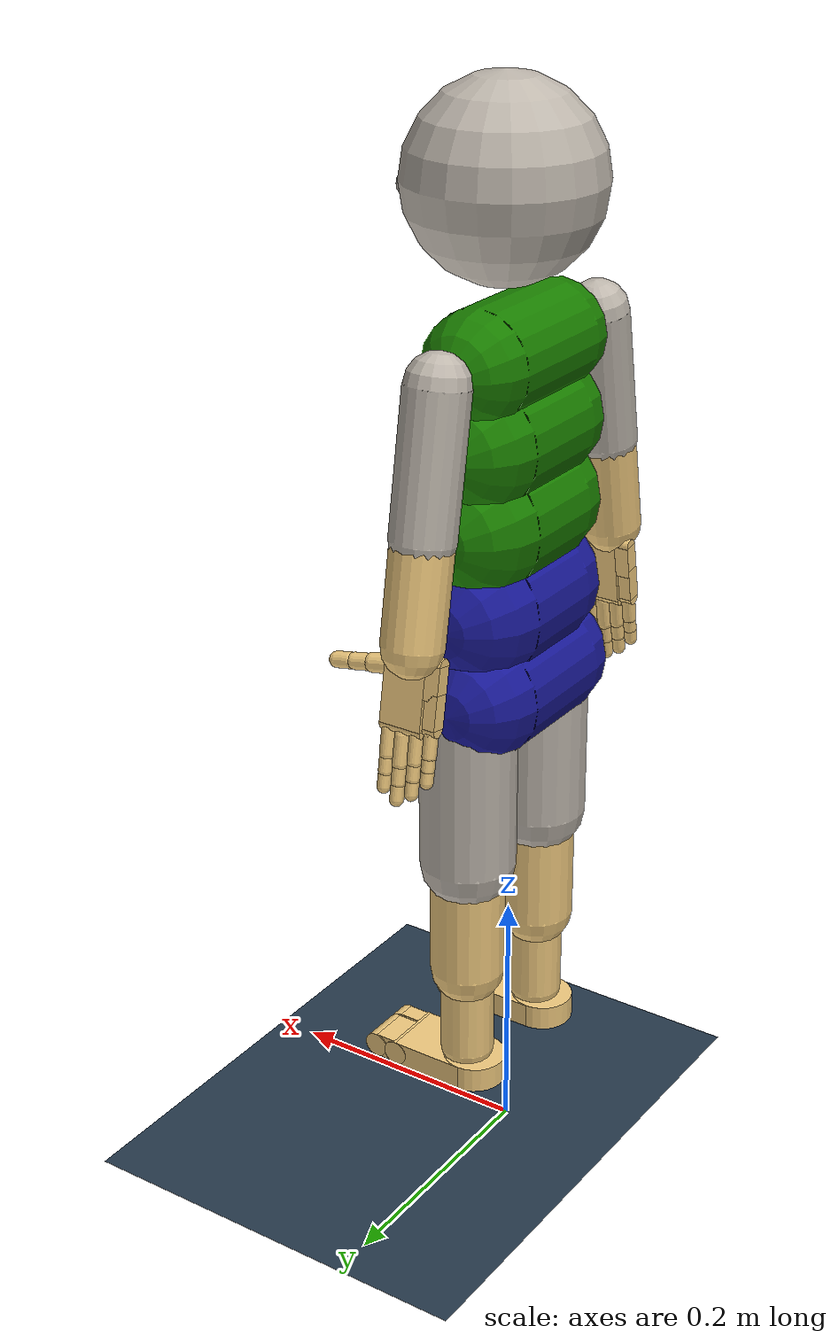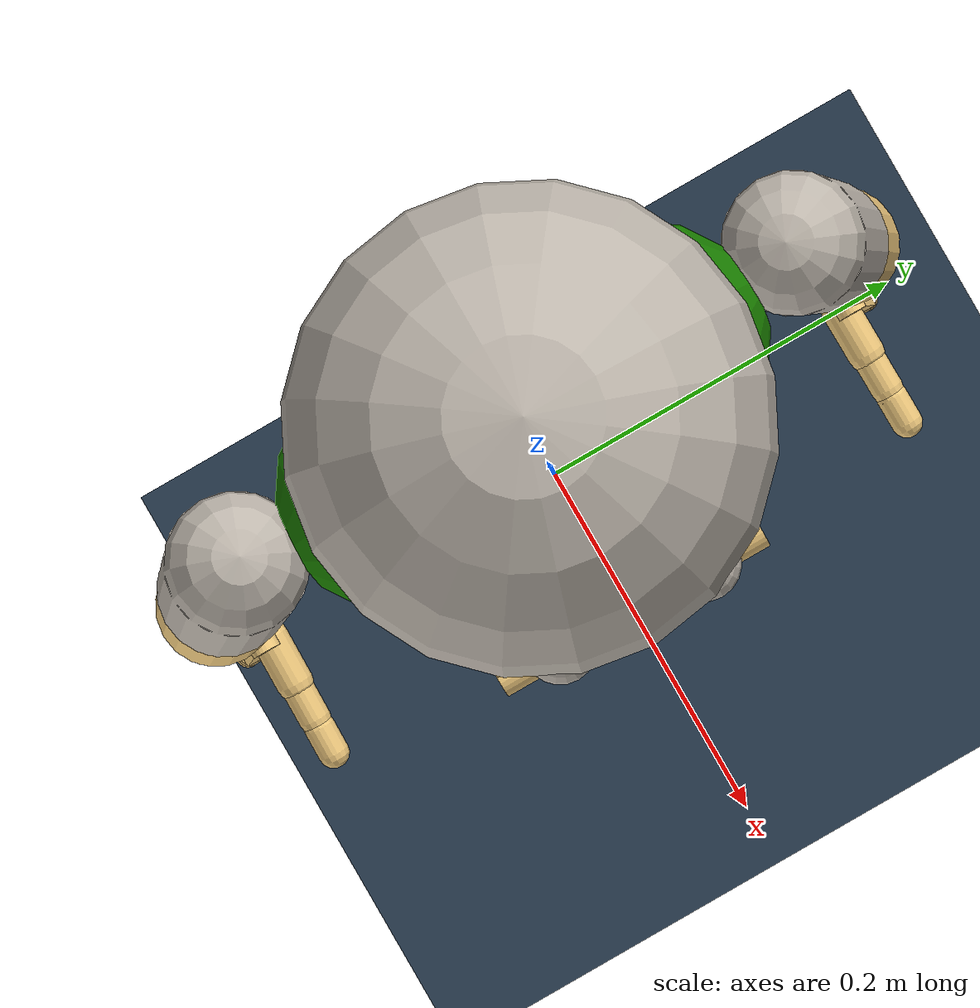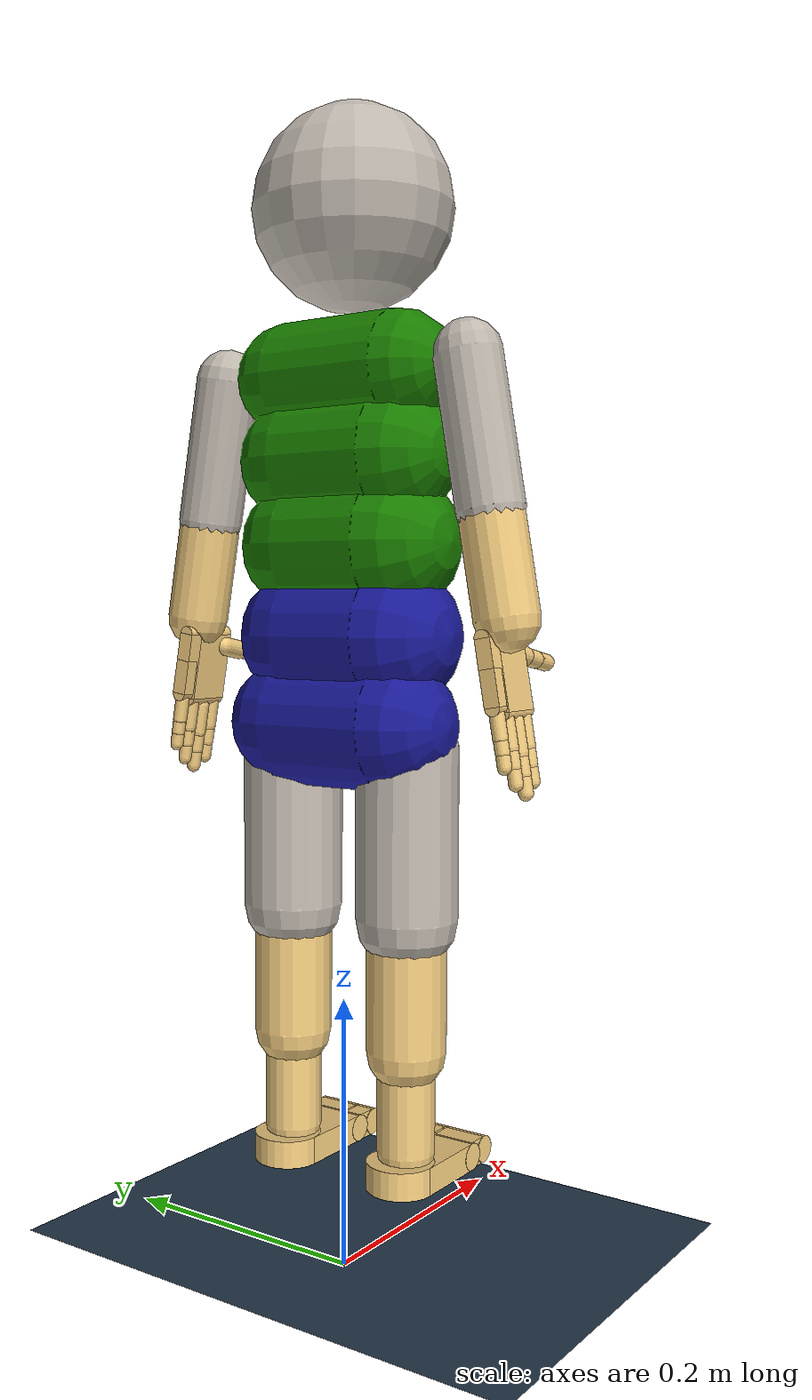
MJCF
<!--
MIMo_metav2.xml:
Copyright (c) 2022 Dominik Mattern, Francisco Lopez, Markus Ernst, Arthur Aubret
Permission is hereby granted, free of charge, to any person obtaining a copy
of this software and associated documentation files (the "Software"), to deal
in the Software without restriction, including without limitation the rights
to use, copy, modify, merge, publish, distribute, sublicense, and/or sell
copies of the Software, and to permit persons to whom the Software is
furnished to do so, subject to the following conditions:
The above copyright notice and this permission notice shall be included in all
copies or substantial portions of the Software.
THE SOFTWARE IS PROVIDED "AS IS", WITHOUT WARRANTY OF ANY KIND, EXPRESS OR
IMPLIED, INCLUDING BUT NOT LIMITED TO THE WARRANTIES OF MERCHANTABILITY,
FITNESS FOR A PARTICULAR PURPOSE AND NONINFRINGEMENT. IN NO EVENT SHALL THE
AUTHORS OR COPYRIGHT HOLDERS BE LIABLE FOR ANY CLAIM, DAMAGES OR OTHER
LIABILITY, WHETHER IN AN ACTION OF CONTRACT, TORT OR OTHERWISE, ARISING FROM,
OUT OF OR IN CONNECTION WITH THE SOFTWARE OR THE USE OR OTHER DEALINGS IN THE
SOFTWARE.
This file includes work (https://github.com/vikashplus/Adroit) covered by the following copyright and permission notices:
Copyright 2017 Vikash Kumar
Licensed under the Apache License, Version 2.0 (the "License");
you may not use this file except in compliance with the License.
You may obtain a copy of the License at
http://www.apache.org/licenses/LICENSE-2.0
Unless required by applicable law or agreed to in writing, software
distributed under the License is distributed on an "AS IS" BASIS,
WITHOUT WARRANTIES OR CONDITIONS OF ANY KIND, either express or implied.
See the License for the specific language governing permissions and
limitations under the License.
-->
<mujoco model="MIMo">

    <compiler inertiafromgeom="true" angle="degree"/>

    <option timestep="0.005" gravity="0 0 0" iterations="50" tolerance="1e-10" solver="Newton" jacobian="dense" cone="elliptic" impratio="1.0"/>

    <size nconmax="1000" njmax="5000" nstack="10000000"/>

    <visual>
        <map force="0.1" zfar="30" znear="0.005"/>
        <rgba haze="0.15 0.25 0.35 1"/>
        <quality shadowsize="4096"/>
        <global offwidth="800" offheight="800"/>
    </visual>

    <default>
        <geom material="matgeom" condim="3" solimp="0.95 0.99 0.001 0.5 1" solref="0.005 1"/>
    </default>

    <asset>
        <texture type="skybox" builtin="gradient" rgb1="0.3 0.5 0.7" rgb2="0 0 0" width="512" height="512"/>

        <texture name="texplane" type="2d" builtin="checker" rgb1=".2 .3 .4" rgb2=".1 0.15 0.2" width="512" height="512" mark="cross" markrgb=".8 .8 .8"/>

        <texture name="texgeom" type="cube" builtin="flat" mark="cross" width="127" height="1278"
            rgb1="0.8 0.6 0.4" rgb2="0.8 0.6 0.4" markrgb="1 1 1" random="0.01"/>

        <material name="matplane" reflectance="0.3" texture="texplane" texrepeat="1 1" texuniform="true"/>

        <material name="matgeom" texture="texgeom" texuniform="true" rgba="0.8 0.6 .4 1"/>

		<material name="matmocap" texture="texgeom" texuniform="true" rgba="0.5 0 0.5 0.5"/>

    </asset>

	<!-- Import everything except the kinematic tree -->
	<include file="mimo/MIMo_metav2.xml"></include>

    <worldbody>
        <geom name="floor" pos="0 0 0" size="0 0 .25" type="plane" material="matplane" condim="3"/>

        <light directional="false" diffuse=".4 .4 .4" specular="0 0 0" pos="0 0 10" dir="0 0 -1" castshadow="false"/>
        <light mode="targetbodycom" target="upper_body" directional="false" diffuse=".8 .8 .8" specular="0.3 0.3 0.3" pos="0 0 5.0" dir="0 0 -1"/>

		<!-- The location and orientation of the base model can be set using this body -->
		<body name="mimo_location" pos="0 0 .4" euler="0 0 0">
			<freejoint name="mimo_orientation"/>
			<include file="mimo/MIMo_modelv2.xml"></include> <!-- Import the actual model-->
		</body>

    </worldbody>

    <equality>
		<weld body1="hip"/>
	</equality>

</mujoco>

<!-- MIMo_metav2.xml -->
<mujoco model="MIMo">

	<!-- We use the first three user values on actuators to store the muscle model parameters. The first is VMAX, the next two are FMAX.-->
	<size nuser_actuator="3" />

	<default>
		<default class="mimo">
        	<joint limited="true" damping=".1" stiffness=".1" armature="0.001" solimplimit="0.98 0.99 0.001 .5 1" solreflimit="0.02 1"/>
        	<geom condim="3" material="skin" friction="1 0.005 0.0002" solimp="0.95 0.99 0.001 0.5 1" solref="0.005 1"/>
        	<motor ctrlrange="-1 1" ctrllimited="true" forcelimited="true"/>
    	</default>
	</default>

    <asset>

		<texture name="tex_head_default" type="cube" fileright="tex/head_front.png" fileleft="tex/head_back.png" fileup="tex/head_left.png" filedown="tex/head_right.png" filefront="tex/head_top.png" rgb1="0.95 .8 .5"/>
		<texture name="tex_head_happy" type="cube" fileright="tex/head_front_happy.png" fileleft="tex/head_back.png" fileup="tex/head_left.png" filedown="tex/head_right.png" filefront="tex/head_top.png" rgb1="0.95 .8 .5"/>
		<texture name="tex_head_sad" type="cube" fileright="tex/head_front_sad.png" fileleft="tex/head_back.png" fileup="tex/head_left.png" filedown="tex/head_right.png" filefront="tex/head_top.png" rgb1="0.95 .8 .5"/>
		<texture name="tex_head_surprised" type="cube" fileright="tex/head_front_surprised.png" fileleft="tex/head_back.png" fileup="tex/head_left.png" filedown="tex/head_right.png" filefront="tex/head_top.png" rgb1="0.95 .8 .5"/>
		<texture name="tex_head_angry" type="cube" fileright="tex/head_front_angry.png" fileleft="tex/head_back.png" fileup="tex/head_left.png" filedown="tex/head_right.png" filefront="tex/head_top.png" rgb1="0.95 .8 .5"/>
		<texture name="tex_head_disgusted" type="cube" fileright="tex/head_front_disgusted.png" fileleft="tex/head_back.png" fileup="tex/head_left.png" filedown="tex/head_right.png" filefront="tex/head_top.png" rgb1="0.95 .8 .5"/>
		<texture name="tex_head_scared" type="cube" fileright="tex/head_front_scared.png" fileleft="tex/head_back.png" fileup="tex/head_left.png" filedown="tex/head_right.png" filefront="tex/head_top.png" rgb1="0.95 .8 .5"/>
		<texture name="tex_top_sleeve" type="cube" fileright="tex/sleeve_right.png" fileleft="tex/sleeve_left.png" fileup="tex/sleeve_up.png" filedown="tex/sleeve_down.png" filefront="tex/sleeve_front.png" fileback="tex/sleeve_back.png" rgb1="0.95 .8 .5"/>
		<texture name="tex_pants_leg" type="cube" fileright="tex/leg_right.png" fileleft="tex/leg_left.png" fileup="tex/leg_up.png" filedown="tex/leg_down.png" filefront="tex/leg_front.png" fileback="tex/leg_back.png" rgb1="0.95 .8 .5"/>
		<texture name="tex_eye_left" type="cube" fileright="tex/eye_pupil_left.png" rgb1="1 1 1"/>
		<texture name="tex_eye_right" type="cube" fileright="tex/eye_pupil_right.png" rgb1="1 1 1"/>

		<material name="skin" rgba="0.95 0.8 0.5 1" specular=".15" shininess=".7"/>
		<material name="buttons" rgba=".05 .05 .05 1" specular=".9" shininess=".9"/>
		<material name="head" texture="tex_head_default" texuniform="true" specular=".0" shininess=".0"/>
		<material name="top_up" rgba=".1 .5 0.0 1" specular=".0" shininess=".0"/>
		<material name="top_middle" rgba=".1 .5 0.0 1" specular=".0" shininess=".0"/>
		<material name="top_down" rgba=".1 .5 0.0 1" specular=".0" shininess=".0"/>
		<material name="top_sleeve" texture="tex_top_sleeve" texuniform="true" specular=".0" shininess=".0"/>
		<material name="pants_up" rgba="0.1 0.1 0.6 1" specular=".0" shininess=".0"/>
		<material name="pants_down" rgba="0.1 0.1 0.6 1" specular=".0" shininess=".0"/>
		<material name="pants_leg" texture="tex_pants_leg" texuniform="true" specular=".0" shininess=".0"/>
		<material name="eye_left" texture="tex_eye_left" texuniform="true" specular=".0" shininess=".0"/>
		<material name="eye_right" texture="tex_eye_right" texuniform="true" specular=".0" shininess=".0"/>

    </asset>

	<!-- Internal contacts should not have friction to reduce "getting stuck" on ourselves-->
	<contact>
		<pair geom1="lb" geom2="ub1" condim="1"/>
		<exclude body1="left_eye" body2="upper_body"/>
		<exclude body1="right_eye" body2="upper_body"/>
		<exclude body1="chest" body2="head"/>
	</contact>

	<tendon>
		<fixed class="mimo" name="hip_bend" limited="true" range="-.01 .01">
			<joint joint="robot:hip_bend1" coef="1"/>
			<joint joint="robot:hip_bend2" coef="-1"/>
		</fixed>
		<fixed class="mimo" name="hip_rotation" limited="true" range="-.01 .01">
			<joint joint="robot:hip_rot1" coef="1"/>
			<joint joint="robot:hip_rot2" coef="-1"/>
		</fixed>
		<fixed class="mimo" name="hip_lean" limited="true" range="-.01 .01">
			<joint joint="robot:hip_lean1" coef="1"/>
			<joint joint="robot:hip_lean2" coef="-.5"/>
		</fixed>

		<fixed class="mimo" name="head_limits1" limited="true" range="-2.1 2.1">
			<joint joint="robot:head_swivel" coef="1"/>
			<joint joint="robot:head_tilt_side" coef="1"/>
		</fixed>
		<fixed class="mimo" name="head_limits2" limited="true" range="-2.1 2.1">
			<joint joint="robot:head_tilt" coef="1"/>
			<joint joint="robot:head_tilt_side" coef="1"/>
		</fixed>
		<fixed class="mimo" name="head_limits3" limited="true" range="-2.1 2.1">
			<joint joint="robot:head_swivel" coef="1"/>
			<joint joint="robot:head_tilt" coef="1"/>
		</fixed>
		<fixed class="mimo" name="head_limits1_sym" limited="true" range="-2.1 2.1">
			<joint joint="robot:head_swivel" coef="1"/>
			<joint joint="robot:head_tilt_side" coef="-1"/>
		</fixed>
		<fixed class="mimo" name="head_limits2_sym" limited="true" range="-2.1 2.1">
			<joint joint="robot:head_tilt" coef="1"/>
			<joint joint="robot:head_tilt_side" coef="-1"/>
		</fixed>
		<fixed class="mimo" name="head_limits3_sym" limited="true" range="-2.1 2.1">
			<joint joint="robot:head_swivel" coef="1"/>
			<joint joint="robot:head_tilt" coef="-1"/>
		</fixed>
	</tendon>

	<sensor>
		<accelerometer name="vestibular_acc" site="vestibular"/>
		<gyro name="vestibular_gyro" site="vestibular"/>

		<torque name="proprio:neck" site="torque_neck"/>
		<torque name="proprio:left_eye" site="torque_left_eye"/>
		<torque name="proprio:right_eye" site="torque_right_eye"/>

		<torque name="proprio:chest" site="torque_chest"/>
		<torque name="proprio:trunk_upper" site="torque_ub"/>
		<torque name="proprio:trunk_lower" site="torque_lb"/>

		<torque name="proprio:right_shoulder" site="torque_right_shoulder"/>
		<torque name="proprio:right_elbow" site="torque_right_elbow"/>
		<torque name="proprio:right_wrist" site="torque_right_wrist"/>

		<torque name="proprio:right_ff_knuckle" site="torque_right_ff_knuckle"/>
		<torque name="proprio:right_ff_middle" site="torque_right_ff_middle"/>
		<torque name="proprio:right_ff_distal" site="torque_right_ff_distal"/>
		<torque name="proprio:right_mf_knuckle" site="torque_right_mf_knuckle"/>
		<torque name="proprio:right_mf_middle" site="torque_right_mf_middle"/>
		<torque name="proprio:right_mf_distal" site="torque_right_mf_distal"/>
		<torque name="proprio:right_rf_knuckle" site="torque_right_rf_knuckle"/>
		<torque name="proprio:right_rf_middle" site="torque_right_rf_middle"/>
		<torque name="proprio:right_rf_distal" site="torque_right_rf_distal"/>
		<torque name="proprio:right_lf_meta" site="torque_right_lf_meta"/>
		<torque name="proprio:right_lf_knuckle" site="torque_right_lf_knuckle"/>
		<torque name="proprio:right_lf_middle" site="torque_right_lf_middle"/>
		<torque name="proprio:right_lf_distal" site="torque_right_lf_distal"/>
		<torque name="proprio:right_th_base" site="torque_right_th_base"/>
		<torque name="proprio:right_th_hub" site="torque_right_th_hub"/>
		<torque name="proprio:right_th_distal" site="torque_right_th_distal"/>

		<torque name="proprio:left_shoulder" site="torque_left_shoulder"/>
		<torque name="proprio:left_elbow" site="torque_left_elbow"/>
		<torque name="proprio:left_wrist" site="torque_left_wrist"/>

		<torque name="proprio:left_ff_knuckle" site="torque_left_ff_knuckle"/>
		<torque name="proprio:left_ff_middle" site="torque_left_ff_middle"/>
		<torque name="proprio:left_ff_distal" site="torque_left_ff_distal"/>
		<torque name="proprio:left_mf_knuckle" site="torque_left_mf_knuckle"/>
		<torque name="proprio:left_mf_middle" site="torque_left_mf_middle"/>
		<torque name="proprio:left_mf_distal" site="torque_left_mf_distal"/>
		<torque name="proprio:left_rf_knuckle" site="torque_left_rf_knuckle"/>
		<torque name="proprio:left_rf_middle" site="torque_left_rf_middle"/>
		<torque name="proprio:left_rf_distal" site="torque_left_rf_distal"/>
		<torque name="proprio:left_lf_meta" site="torque_left_lf_meta"/>
		<torque name="proprio:left_lf_knuckle" site="torque_left_lf_knuckle"/>
		<torque name="proprio:left_lf_middle" site="torque_left_lf_middle"/>
		<torque name="proprio:left_lf_distal" site="torque_left_lf_distal"/>
		<torque name="proprio:left_th_base" site="torque_left_th_base"/>
		<torque name="proprio:left_th_hub" site="torque_left_th_hub"/>
		<torque name="proprio:left_th_distal" site="torque_left_th_distal"/>

		<torque name="proprio:right_hip" site="torque_right_hip"/>
		<torque name="proprio:right_knee" site="torque_right_knee"/>
		<torque name="proprio:right_ankle" site="torque_right_ankle"/>
		<torque name="proprio:right_toes" site="torque_right_toes"/>
		<torque name="proprio:right_big_toe" site="torque_right_big_toe"/>

		<torque name="proprio:left_hip" site="torque_left_hip"/>
		<torque name="proprio:left_knee" site="torque_left_knee"/>
		<torque name="proprio:left_ankle" site="torque_left_ankle"/>
		<torque name="proprio:left_toes" site="torque_left_toes"/>
		<torque name="proprio:left_big_toe" site="torque_left_big_toe"/>
	</sensor>

    <actuator>
		<!-- 12 + 2*30 + 2*9 = 90 degrees of freedom-->
		<motor class="mimo"	name="act:hip_bend" 						joint="robot:hip_bend1" 				gear="10.58" 		forcerange="-1 .765"	user=".8574 32.93 22.97"/>
		<motor class="mimo"	name="act:hip_twist" 						joint="robot:hip_rot1" 					gear="3.63" 		forcerange="-1 1"		user="1.699 8.136 8.136"/>
		<motor class="mimo"	name="act:hip_lean" 						joint="robot:hip_lean1" 				gear="7.25" 		forcerange="-1 1"		user="1.278 1.264 1.264"/>

		<motor class="mimo"	name="act:chest_twist" 						joint="robot:chest_rot" 				gear="0.36" 		forcerange="-1 1"		user="1.699 8.136 8.136"/>
		<motor class="mimo"	name="act:chest_lean" 						joint="robot:chest_lean" 				gear="0.72" 		forcerange="-1 1"		user="1.278 1.264 1.264"/>

		<motor class="mimo"	name="act:head_swivel" 						joint="robot:head_swivel" 				gear="1.8" 			forcerange="-1 1"		user=".6665 24.87 24.87"/>
		<motor class="mimo"	name="act:head_tilt" 						joint="robot:head_tilt" 				gear="3.3" 			forcerange="-1 .55"		user=".9338 31.39 16.86"/>
		<motor class="mimo"	name="act:head_tilt_side" 					joint="robot:head_tilt_side" 			gear="1.8" 			forcerange="-1 1"		user="1.068 15.69 15.69"/>

		<motor class="mimo" name="act:left_eye_horizontal" 				joint="robot:left_eye_horizontal" 		gear=".0054" 		forcerange="-1 1"		user="5.110 .03025 .03025"/>
		<motor class="mimo" name="act:left_eye_vertical" 				joint="robot:left_eye_vertical" 		gear=".0054" 		forcerange="-1 1"		user="6.179 .02619 .02771"/>
		<motor class="mimo" name="act:left_eye_torsional" 				joint="robot:left_eye_torsional" 		gear=".0037" 		forcerange="-1 1"		user="25.03 .003686 .003686"/>
		<motor class="mimo" name="act:right_eye_horizontal" 			joint="robot:right_eye_horizontal" 		gear=".0054" 		forcerange="-1 1"		user="5.110 .03025 .03025"/>
		<motor class="mimo" name="act:right_eye_vertical" 				joint="robot:right_eye_vertical" 		gear=".0054" 		forcerange="-1 1"		user="6.179 .02619 .02771"/>
		<motor class="mimo" name="act:right_eye_torsional" 				joint="robot:right_eye_torsional" 		gear=".0037" 		forcerange="-1 1"		user="25.03 .003686 .003686"/>

		<motor class="mimo"	name="act:right_shoulder_horizontal" 		joint="robot:right_shoulder_horizontal" gear="1.8" 			forcerange="-1 1"		user="1.811 18.80 15.30"/>
		<motor class="mimo"	name="act:right_shoulder_abduction" 		joint="robot:right_shoulder_ad_ab" 		gear="4" 			forcerange="-.6875 1"	user=".8793 44.17 69.23"/>
		<motor class="mimo"	name="act:right_shoulder_internal" 			joint="robot:right_shoulder_rotation" 	gear="2.5" 			forcerange="-1 .64"		user="1.498 25.09 17.10"/>
		<motor class="mimo"	name="act:right_elbow" 						joint="robot:right_elbow" 				gear="3.6" 			forcerange="-1 .83"		user="1.566 35.43 27.04"/>
		<motor class="mimo"	name="act:right_wrist_rotation" 			joint="robot:right_hand1" 				gear=".7"			forcerange="-1 1"		user="1.513 7.842 7.842"/>
		<motor class="mimo"	name="act:right_wrist_flexion" 				joint="robot:right_hand2" 				gear="1.24"			forcerange="-1 .57"		user="1.455 13.66 7.874"/>
		<motor class="mimo"	name="act:right_wrist_ulnar" 				joint="robot:right_hand3" 				gear=".95"			forcerange="-.87 1"		user="2.254 5.155 6.021"/>

		<motor class="mimo"	name="act:right_ff_side" 			 		joint="robot:right_ff_side" 			gear=".05"			forcerange="-1 1"		user="6.217 .1556 .1556"/>
		<motor class="mimo"	name="act:right_ff_knuckle" 			 	joint="robot:right_ff_knuckle"			gear=".0619"		forcerange="-.345 1"	user="4.368 .1422 .4378"/>
		<motor class="mimo"	name="act:right_ff_middle" 				 	joint="robot:right_ff_middle"			gear=".02063"		forcerange="-.345 1"	user="3.493 .04684 .1339"/>
		<motor class="mimo"	name="act:right_ff_distal" 				 	joint="robot:right_ff_distal"			gear=".01548"		forcerange="-.345 1"	user="2.539 .03054 .07747"/>

		<motor class="mimo"	name="act:right_mf_side" 			 		joint="robot:right_mf_side" 			gear=".05"			forcerange="-1 1"		user="5.375 .1556 .1556"/>
		<motor class="mimo"	name="act:right_mf_knuckle" 			 	joint="robot:right_mf_knuckle"			gear=".117"			forcerange="-.345 1"	user="4.325 .2687 .8275"/>
		<motor class="mimo"	name="act:right_mf_middle" 			 		joint="robot:right_mf_middle"			gear=".039"			forcerange="-.345 1"	user="3.375 .08855 .2532"/>
		<motor class="mimo"	name="act:right_mf_distal" 				 	joint="robot:right_mf_distal"			gear=".02925"		forcerange="-.345 1"	user="2.577 .05771 .1464"/>

		<motor class="mimo"	name="act:right_rf_side"  					joint="robot:right_rf_side" 			gear=".05"			forcerange="-1 1"		user="4.984 .1556 .1556"/>
		<motor class="mimo"	name="act:right_rf_knuckle" 			 	joint="robot:right_rf_knuckle"			gear=".078"			forcerange="-.345 1"	user="2.817 .1791 .5517"/>
		<motor class="mimo"	name="act:right_rf_middle" 			 		joint="robot:right_rf_middle" 			gear=".026"			forcerange="-.345 1"	user="3.007 .05903 .1688"/>
		<motor class="mimo"	name="act:right_rf_distal" 				 	joint="robot:right_rf_distal" 			gear=".0195"		forcerange="-.345 1"	user="2.313 .03847 .09759"/>

		<motor class="mimo"	name="act:right_lf_side" 					joint="robot:right_lf_side" 			gear=".05" 			forcerange="-1 1"		user="5.282 .1556 .1556"/>
		<motor class="mimo"	name="act:right_lf_meta" 					joint="robot:right_lf_meta" 			gear=".064" 		forcerange="-.345 1"	user="6.855 .07962 .1508"/>
		<motor class="mimo"	name="act:right_lf_knuckle" 			 	joint="robot:right_lf_knuckle" 			gear=".0196"		forcerange="-.345 1"	user="2.337 .04502 .1386"/>
		<motor class="mimo"	name="act:right_lf_middle" 				 	joint="robot:right_lf_middle" 			gear=".00653"		forcerange="-.345 1"	user="2.566 .01483 .04239"/>
		<motor class="mimo"	name="act:right_lf_distal" 				 	joint="robot:right_lf_distal" 			gear=".00490"		forcerange="-.345 1"	user="2.001 .009666 .02452"/>

		<motor class="mimo"	name="act:right_thumb_side" 			 	joint="robot:right_th_swivel" 			gear=".373"			forcerange="-.345 1"	user="3.491 1.117 2.604"/>
		<motor class="mimo"	name="act:right_thumb_add" 					joint="robot:right_th_adduction" 		gear=".134" 		forcerange="-1 1"		user="5.646 .4969 .5024"/>
		<motor class="mimo"	name="act:right_thumb_pivot" 				joint="robot:right_th_pivot" 			gear=".1" 			forcerange="-1 1"		user="9.055 .1868 .1868"/>
		<motor class="mimo"	name="act:right_thumb_middle" 			 	joint="robot:right_th_middle" 			gear=".126"			forcerange="-.345 1"	user="3.877 .2433 .7065"/>
		<motor class="mimo"	name="act:right_thumb_distal" 			 	joint="robot:right_th_distal" 			gear=".0945"		forcerange="-.345 1"	user="3.392 .2053 .4959"/>

		<motor class="mimo"	name="act:left_shoulder_horizontal" 		joint="robot:left_shoulder_horizontal" 	gear="1.8" 			forcerange="-1 1"		user="1.811 18.80 15.30"/>
		<motor class="mimo"	name="act:left_shoulder_abduction" 			joint="robot:left_shoulder_ad_ab" 		gear="4" 			forcerange="-.6875 1"	user=".8793 44.17 69.23"/>
		<motor class="mimo"	name="act:left_shoulder_internal" 			joint="robot:left_shoulder_rotation" 	gear="2.5" 			forcerange="-1 .64"		user="1.498 25.09 17.10"/>
		<motor class="mimo"	name="act:left_elbow" 						joint="robot:left_elbow" 				gear="3.6" 			forcerange="-1 .83"		user="1.566 35.43 27.04"/>
		<motor class="mimo"	name="act:left_wrist_rotation" 				joint="robot:left_hand1"  				gear=".7"			forcerange="-1 1"		user="1.513 7.842 7.842"/>
		<motor class="mimo"	name="act:left_wrist_flexion" 				joint="robot:left_hand2"  				gear="1.24"			forcerange="-1 .57"		user="1.455 13.66 7.874"/>
		<motor class="mimo"	name="act:left_wrist_ulnar" 				joint="robot:left_hand3"  				gear=".95"			forcerange="-.87 1"		user="2.254 5.155 6.021"/>

		<motor class="mimo"	name="act:left_ff_side" 		 			joint="robot:left_ff_side" 				gear=".05"			forcerange="-1 1"		user="6.217 .1556 .1556"/>
		<motor class="mimo"	name="act:left_ff_knuckle" 				 	joint="robot:left_ff_knuckle" 			gear=".0619"		forcerange="-.345 1"	user="4.368 .1422 .4378"/>
		<motor class="mimo"	name="act:left_ff_middle" 				 	joint="robot:left_ff_middle" 			gear=".02063"		forcerange="-.345 1"	user="3.493 .04684 .1339"/>
		<motor class="mimo"	name="act:left_ff_distal" 				 	joint="robot:left_ff_distal" 			gear=".01548"		forcerange="-.345 1"	user="2.539 .03054 .07747"/>

		<motor class="mimo"	name="act:left_mf_side" 		 			joint="robot:left_mf_side" 				gear=".05"			forcerange="-1 1"		user="5.375 .1556 .1556"/>
		<motor class="mimo"	name="act:left_mf_knuckle" 			 		joint="robot:left_mf_knuckle" 			gear=".117"			forcerange="-.345 1"	user="4.325 .2687 .8275"/>
		<motor class="mimo"	name="act:left_mf_middle" 			 		joint="robot:left_mf_middle" 			gear=".039"			forcerange="-.345 1"	user="3.375 .08855 .2532"/>
		<motor class="mimo"	name="act:left_mf_distal" 				 	joint="robot:left_mf_distal" 			gear=".02925"		forcerange="-.345 1"	user="2.577 .05771 .1464"/>

		<motor class="mimo"	name="act:left_rf_side" 		 			joint="robot:left_rf_side" 				gear=".05"			forcerange="-1 1"		user="4.984 .1556 .1556"/>
		<motor class="mimo"	name="act:left_rf_knuckle" 			 		joint="robot:left_rf_knuckle" 			gear=".078"			forcerange="-.345 1"	user="2.817 .1791 .5517"/>
		<motor class="mimo"	name="act:left_rf_middle" 			 		joint="robot:left_rf_middle" 			gear=".026"			forcerange="-.345 1"	user="3.007 .05903 .1688"/>
		<motor class="mimo"	name="act:left_rf_distal" 			 		joint="robot:left_rf_distal" 			gear=".0195"		forcerange="-.345 1"	user="2.313 .03847 .09759"/>

		<motor class="mimo"	name="act:left_lf_side" 		 			joint="robot:left_lf_side" 				gear=".05"			forcerange="-1 1"		user="5.282 .1556 .1556"/>
		<motor class="mimo"	name="act:left_lf_meta" 			 		joint="robot:left_lf_meta" 				gear=".064"			forcerange="-.345 1"	user="6.855 .07962 .1508"/>
		<motor class="mimo"	name="act:left_lf_knuckle" 				 	joint="robot:left_lf_knuckle" 			gear=".0196"		forcerange="-.345 1"	user="2.337 .04502 .1386"/>
		<motor class="mimo"	name="act:left_lf_middle" 				 	joint="robot:left_lf_middle" 			gear=".00653"		forcerange="-.345 1"	user="2.566 .01483 .04239"/>
		<motor class="mimo"	name="act:left_lf_distal" 				 	joint="robot:left_lf_distal" 			gear=".00490"		forcerange="-.345 1"	user="2.001 .009666 .02452"/>

		<motor class="mimo"	name="act:left_thumb_side" 			 		joint="robot:left_th_swivel" 			gear=".373"			forcerange="-.345 1"	user="3.491 1.117 2.604"/>
		<motor class="mimo"	name="act:left_thumb_add" 					joint="robot:left_th_adduction" 		gear=".134" 		forcerange="-1 1"		user="5.646 .4969 .5024"/>
		<motor class="mimo"	name="act:left_thumb_pivot" 				joint="robot:left_th_pivot" 			gear=".1" 			forcerange="-1 1"		user="9.055 .1868 .1868"/>
		<motor class="mimo"	name="act:left_thumb_middle" 			 	joint="robot:left_th_middle" 			gear=".126"			forcerange="-.345 1"	user="3.877 .2433 .7065"/>
		<motor class="mimo"	name="act:left_thumb_distal" 			 	joint="robot:left_th_distal" 			gear=".0945"		forcerange="-.345 1"	user="3.392 .2053 .4959"/>

		<motor class="mimo"	name="act:right_hip_flex" 					joint="robot:right_hip1" 				gear="8" 			forcerange="-1 1"		user="1.083 71.25 92.49"/>
		<motor class="mimo"	name="act:right_hip_abduction" 				joint="robot:right_hip2" 				gear="6.24" 		forcerange="-1 1"		user="1.488 24.81 29.20"/>
		<motor class="mimo"	name="act:right_hip_rotation" 				joint="robot:right_hip3" 				gear="3.54" 		forcerange="-.75 1"		user="1.860 12.32 15.78"/>
		<motor class="mimo"	name="act:right_knee" 						joint="robot:right_knee" 				gear="10" 			forcerange="-.65 1"		user="1.450 63.16 89.27"/>
		<motor class="mimo"	name="act:right_foot_flexion" 				joint="robot:right_foot1" 				gear="3.78"			forcerange="-1 .5"		user="1.430 21.34 11.87"/>
		<motor class="mimo"	name="act:right_foot_inversion" 			joint="robot:right_foot2" 				gear="1.16"			forcerange="-.91 1"		user="1.988 4.184 4.645"/>
		<motor class="mimo"	name="act:right_foot_rotation" 				joint="robot:right_foot3"	 			gear="1.2"			forcerange="-1 1"		user="2.688 3.868 3.625"/>
		<motor class="mimo"	name="act:right_big_toe" 					joint="robot:right_big_toe"	 			gear=".165"			forcerange="-1 .3"		user="1.774 1.473 .4220"/>
		<motor class="mimo"	name="act:right_toes" 						joint="robot:right_toes"	 			gear=".165"			forcerange="-1 .3"		user="1.805 1.473 .4220"/>

		<motor class="mimo"	name="act:left_hip_flex" 					joint="robot:left_hip1" 				gear="8" 			forcerange="-1 1"		user="1.083 71.25 92.49"/>
		<motor class="mimo"	name="act:left_hip_abduction" 				joint="robot:left_hip2" 				gear="6.24" 		forcerange="-1 1"		user="1.488 24.81 29.20"/>
		<motor class="mimo"	name="act:left_hip_rotation" 				joint="robot:left_hip3"					gear="3.54" 		forcerange="-.75 1"		user="1.860 12.32 15.78"/>
		<motor class="mimo"	name="act:left_knee" 						joint="robot:left_knee" 				gear="10" 			forcerange="-.65 1"		user="1.450 63.16 89.27"/>
		<motor class="mimo"	name="act:left_foot_flexion" 				joint="robot:left_foot1" 				gear="3.78"			forcerange="-1 .5"		user="1.430 21.34 11.87"/>
		<motor class="mimo"	name="act:left_foot_inversion" 				joint="robot:left_foot2" 				gear="1.16"			forcerange="-.91 1"		user="1.988 4.184 4.645"/>
		<motor class="mimo"	name="act:left_foot_rotation" 				joint="robot:left_foot3" 				gear="1.2"			forcerange="-1 1"		user="2.688 3.868 3.625"/>
		<motor class="mimo"	name="act:left_toes" 						joint="robot:left_toes"	 				gear=".165"			forcerange="-1 .3"		user="1.774 1.473 .4220"/>
		<motor class="mimo"	name="act:left_big_toe" 					joint="robot:left_big_toe"	 			gear=".165"			forcerange="-1 .3"		user="1.805 1.473 .4220"/>
	</actuator>

	<equality> <!-- These contraints are used for joint locking during runtime -->
		<joint name="robot:hip_lean1" 					joint1="robot:hip_lean1" active="false" polycoef="0 1 0 0 0" solimp="0.95 0.99999 0.001 0.5 2"/>
		<joint name="robot:hip_rot1" 					joint1="robot:hip_rot1" active="false" polycoef="0 1 0 0 0" solimp="0.95 0.99999 0.001 0.5 2"/>
		<joint name="robot:hip_bend1" 					joint1="robot:hip_bend1" active="false" polycoef="0 1 0 0 0" solimp="0.95 0.99999 0.001 0.5 2"/>
		<joint name="robot:hip_lean2" 					joint1="robot:hip_lean2" active="false" polycoef="0 1 0 0 0" solimp="0.95 0.99999 0.001 0.5 2"/>
		<joint name="robot:hip_rot2" 					joint1="robot:hip_rot2" active="false" polycoef="0 1 0 0 0" solimp="0.95 0.99999 0.001 0.5 2"/>
		<joint name="robot:hip_bend2" 					joint1="robot:hip_bend2" active="false" polycoef="0 1 0 0 0" solimp="0.95 0.99999 0.001 0.5 2"/>
		<joint name="robot:head_swivel" 				joint1="robot:head_swivel" active="false" polycoef="0 1 0 0 0" solimp="0.95 0.99999 0.001 0.5 2"/>
		<joint name="robot:head_tilt" 					joint1="robot:head_tilt" active="false" polycoef="0 1 0 0 0" solimp="0.95 0.99999 0.001 0.5 2"/>
		<joint name="robot:head_tilt_side" 				joint1="robot:head_tilt_side" active="false" polycoef="0 1 0 0 0" solimp="0.95 0.99999 0.001 0.5 2"/>
		<joint name="robot:left_eye_horizontal" 		joint1="robot:left_eye_horizontal" active="false" polycoef="0 1 0 0 0" solimp="0.95 0.99999 0.001 0.5 2"/>
		<joint name="robot:left_eye_vertical" 			joint1="robot:left_eye_vertical" active="false" polycoef="0 1 0 0 0" solimp="0.95 0.99999 0.001 0.5 2"/>
		<joint name="robot:left_eye_torsional" 			joint1="robot:left_eye_torsional" active="false" polycoef="0 1 0 0 0" solimp="0.95 0.99999 0.001 0.5 2"/>
		<joint name="robot:right_eye_horizontal" 		joint1="robot:right_eye_horizontal" active="false" polycoef="0 1 0 0 0" solimp="0.95 0.99999 0.001 0.5 2"/>
		<joint name="robot:right_eye_vertical" 			joint1="robot:right_eye_vertical" active="false" polycoef="0 1 0 0 0" solimp="0.95 0.99999 0.001 0.5 2"/>
		<joint name="robot:right_eye_torsional" 		joint1="robot:right_eye_torsional" active="false" polycoef="0 1 0 0 0" solimp="0.95 0.99999 0.001 0.5 2"/>

		<joint name="robot:right_shoulder_horizontal" 	joint1="robot:right_shoulder_horizontal" active="false" polycoef="0 1 0 0 0" solimp="0.95 0.99999 0.001 0.5 2"/>
		<joint name="robot:right_shoulder_ad_ab" 		joint1="robot:right_shoulder_ad_ab" active="false" polycoef="0 1 0 0 0" solimp="0.95 0.99999 0.001 0.5 2"/>
		<joint name="robot:right_shoulder_rotation" 	joint1="robot:right_shoulder_rotation" active="false" polycoef="0 1 0 0 0" solimp="0.95 0.99999 0.001 0.5 2"/>
		<joint name="robot:right_elbow" 				joint1="robot:right_elbow" active="false" polycoef="0 1 0 0 0" solimp="0.95 0.99999 0.001 0.5 2"/>
		<joint name="robot:right_hand1" 				joint1="robot:right_hand1" active="false" polycoef="0 1 0 0 0" solimp="0.95 0.99999 0.001 0.5 2"/>
		<joint name="robot:right_hand2" 				joint1="robot:right_hand2" active="false" polycoef="0 1 0 0 0" solimp="0.95 0.99999 0.001 0.5 2"/>
		<joint name="robot:right_hand3" 				joint1="robot:right_hand3" active="false" polycoef="0 1 0 0 0" solimp="0.95 0.99999 0.001 0.5 2"/>

		<joint name="robot:right_ff_side" 				joint1="robot:right_ff_side" active="false" polycoef="0 1 0 0 0" solimp="0.95 0.99999 0.001 0.5 2"/>
		<joint name="robot:right_ff_knuckle" 			joint1="robot:right_ff_knuckle" active="false" polycoef="0 1 0 0 0" solimp="0.95 0.99999 0.001 0.5 2"/>
		<joint name="robot:right_ff_middle" 			joint1="robot:right_ff_middle" active="false" polycoef="0 1 0 0 0" solimp="0.95 0.99999 0.001 0.5 2"/>
		<joint name="robot:right_ff_distal" 			joint1="robot:right_ff_distal" active="false" polycoef="0 1 0 0 0" solimp="0.95 0.99999 0.001 0.5 2"/>
		<joint name="robot:right_mf_side" 				joint1="robot:right_mf_side" active="false" polycoef="0 1 0 0 0" solimp="0.95 0.99999 0.001 0.5 2"/>
		<joint name="robot:right_mf_knuckle" 			joint1="robot:right_mf_knuckle" active="false" polycoef="0 1 0 0 0" solimp="0.95 0.99999 0.001 0.5 2"/>
		<joint name="robot:right_mf_middle" 			joint1="robot:right_mf_middle" active="false" polycoef="0 1 0 0 0" solimp="0.95 0.99999 0.001 0.5 2"/>
		<joint name="robot:right_mf_distal" 			joint1="robot:right_mf_distal" active="false" polycoef="0 1 0 0 0" solimp="0.95 0.99999 0.001 0.5 2"/>
		<joint name="robot:right_rf_side" 				joint1="robot:right_rf_side" active="false" polycoef="0 1 0 0 0" solimp="0.95 0.99999 0.001 0.5 2"/>
		<joint name="robot:right_rf_knuckle" 			joint1="robot:right_rf_knuckle" active="false" polycoef="0 1 0 0 0" solimp="0.95 0.99999 0.001 0.5 2"/>
		<joint name="robot:right_rf_middle" 			joint1="robot:right_rf_middle" active="false" polycoef="0 1 0 0 0" solimp="0.95 0.99999 0.001 0.5 2"/>
		<joint name="robot:right_rf_distal" 			joint1="robot:right_rf_distal" active="false" polycoef="0 1 0 0 0" solimp="0.95 0.99999 0.001 0.5 2"/>
		<joint name="robot:right_lf_meta" 				joint1="robot:right_lf_meta" active="false" polycoef="0 1 0 0 0" solimp="0.95 0.99999 0.001 0.5 2"/>
		<joint name="robot:right_lf_side" 				joint1="robot:right_lf_side" active="false" polycoef="0 1 0 0 0" solimp="0.95 0.99999 0.001 0.5 2"/>
		<joint name="robot:right_lf_knuckle" 			joint1="robot:right_lf_knuckle" active="false" polycoef="0 1 0 0 0" solimp="0.95 0.99999 0.001 0.5 2"/>
		<joint name="robot:right_lf_middle" 			joint1="robot:right_lf_middle" active="false" polycoef="0 1 0 0 0" solimp="0.95 0.99999 0.001 0.5 2"/>
		<joint name="robot:right_lf_distal" 			joint1="robot:right_lf_distal" active="false" polycoef="0 1 0 0 0" solimp="0.95 0.99999 0.001 0.5 2"/>
		<joint name="robot:right_th_swivel" 			joint1="robot:right_th_swivel" active="false" polycoef="0 1 0 0 0" solimp="0.95 0.99999 0.001 0.5 2"/>
		<joint name="robot:right_th_adduction" 			joint1="robot:right_th_adduction" active="false" polycoef="0 1 0 0 0" solimp="0.95 0.99999 0.001 0.5 2"/>
		<joint name="robot:right_th_pivot" 				joint1="robot:right_th_pivot" active="false" polycoef="0 1 0 0 0" solimp="0.95 0.99999 0.001 0.5 2"/>
		<joint name="robot:right_th_middle" 			joint1="robot:right_th_middle" active="false" polycoef="0 1 0 0 0" solimp="0.95 0.99999 0.001 0.5 2"/>
		<joint name="robot:right_th_distal" 			joint1="robot:right_th_distal" active="false" polycoef="0 1 0 0 0" solimp="0.95 0.99999 0.001 0.5 2"/>

		<joint name="robot:left_shoulder_horizontal" 	joint1="robot:left_shoulder_horizontal" active="false" polycoef="0 1 0 0 0" solimp="0.95 0.99999 0.001 0.5 2"/>
		<joint name="robot:left_shoulder_ad_ab" 		joint1="robot:left_shoulder_ad_ab" active="false" polycoef="0 1 0 0 0" solimp="0.95 0.99999 0.001 0.5 2"/>
		<joint name="robot:left_shoulder_rotation" 		joint1="robot:left_shoulder_rotation" active="false" polycoef="0 1 0 0 0" solimp="0.95 0.99999 0.001 0.5 2"/>
		<joint name="robot:left_elbow" 					joint1="robot:left_elbow" active="false" polycoef="0 1 0 0 0" solimp="0.95 0.99999 0.001 0.5 2"/>
		<joint name="robot:left_hand1" 					joint1="robot:left_hand1" active="false" polycoef="0 1 0 0 0" solimp="0.95 0.99999 0.001 0.5 2"/>
		<joint name="robot:left_hand2" 					joint1="robot:left_hand2" active="false" polycoef="0 1 0 0 0" solimp="0.95 0.99999 0.001 0.5 2"/>
		<joint name="robot:left_hand3" 					joint1="robot:left_hand3" active="false" polycoef="0 1 0 0 0" solimp="0.95 0.99999 0.001 0.5 2"/>

		<joint name="robot:left_ff_side" 				joint1="robot:left_ff_side" active="false" polycoef="0 1 0 0 0" solimp="0.95 0.99999 0.001 0.5 2"/>
		<joint name="robot:left_ff_knuckle" 			joint1="robot:left_ff_knuckle" active="false" polycoef="0 1 0 0 0" solimp="0.95 0.99999 0.001 0.5 2"/>
		<joint name="robot:left_ff_middle" 				joint1="robot:left_ff_middle" active="false" polycoef="0 1 0 0 0" solimp="0.95 0.99999 0.001 0.5 2"/>
		<joint name="robot:left_ff_distal" 				joint1="robot:left_ff_distal" active="false" polycoef="0 1 0 0 0" solimp="0.95 0.99999 0.001 0.5 2"/>
		<joint name="robot:left_mf_side" 				joint1="robot:left_mf_side" active="false" polycoef="0 1 0 0 0" solimp="0.95 0.99999 0.001 0.5 2"/>
		<joint name="robot:left_mf_knuckle" 			joint1="robot:left_mf_knuckle" active="false" polycoef="0 1 0 0 0" solimp="0.95 0.99999 0.001 0.5 2"/>
		<joint name="robot:left_mf_middle" 				joint1="robot:left_mf_middle" active="false" polycoef="0 1 0 0 0" solimp="0.95 0.99999 0.001 0.5 2"/>
		<joint name="robot:left_mf_distal" 				joint1="robot:left_mf_distal" active="false" polycoef="0 1 0 0 0" solimp="0.95 0.99999 0.001 0.5 2"/>
		<joint name="robot:left_rf_side" 				joint1="robot:left_rf_side" active="false" polycoef="0 1 0 0 0" solimp="0.95 0.99999 0.001 0.5 2"/>
		<joint name="robot:left_rf_knuckle" 			joint1="robot:left_rf_knuckle" active="false" polycoef="0 1 0 0 0" solimp="0.95 0.99999 0.001 0.5 2"/>
		<joint name="robot:left_rf_middle" 				joint1="robot:left_rf_middle" active="false" polycoef="0 1 0 0 0" solimp="0.95 0.99999 0.001 0.5 2"/>
		<joint name="robot:left_rf_distal" 				joint1="robot:left_rf_distal" active="false" polycoef="0 1 0 0 0" solimp="0.95 0.99999 0.001 0.5 2"/>
		<joint name="robot:left_lf_meta" 				joint1="robot:left_lf_meta" active="false" polycoef="0 1 0 0 0" solimp="0.95 0.99999 0.001 0.5 2"/>
		<joint name="robot:left_lf_side" 				joint1="robot:left_lf_side" active="false" polycoef="0 1 0 0 0" solimp="0.95 0.99999 0.001 0.5 2"/>
		<joint name="robot:left_lf_knuckle" 			joint1="robot:left_lf_knuckle" active="false" polycoef="0 1 0 0 0" solimp="0.95 0.99999 0.001 0.5 2"/>
		<joint name="robot:left_lf_middle" 				joint1="robot:left_lf_middle" active="false" polycoef="0 1 0 0 0" solimp="0.95 0.99999 0.001 0.5 2"/>
		<joint name="robot:left_lf_distal" 				joint1="robot:left_lf_distal" active="false" polycoef="0 1 0 0 0" solimp="0.95 0.99999 0.001 0.5 2"/>
		<joint name="robot:left_th_swivel" 				joint1="robot:left_th_swivel" active="false" polycoef="0 1 0 0 0" solimp="0.95 0.99999 0.001 0.5 2"/>
		<joint name="robot:left_th_adduction" 			joint1="robot:left_th_adduction" active="false" polycoef="0 1 0 0 0" solimp="0.95 0.99999 0.001 0.5 2"/>
		<joint name="robot:left_th_pivot" 				joint1="robot:left_th_pivot" active="false" polycoef="0 1 0 0 0" solimp="0.95 0.99999 0.001 0.5 2"/>
		<joint name="robot:left_th_middle" 				joint1="robot:left_th_middle" active="false" polycoef="0 1 0 0 0" solimp="0.95 0.99999 0.001 0.5 2"/>
		<joint name="robot:left_th_distal" 				joint1="robot:left_th_distal" active="false" polycoef="0 1 0 0 0" solimp="0.95 0.99999 0.001 0.5 2"/>

		<joint name="robot:right_hip1" 					joint1="robot:right_hip1" active="false" polycoef="0 1 0 0 0" solimp="0.95 0.99999 0.001 0.5 2"/>
		<joint name="robot:right_hip2" 					joint1="robot:right_hip2" active="false" polycoef="0 1 0 0 0" solimp="0.95 0.99999 0.001 0.5 2"/>
		<joint name="robot:right_hip3" 					joint1="robot:right_hip3" active="false" polycoef="0 1 0 0 0" solimp="0.95 0.99999 0.001 0.5 2"/>
		<joint name="robot:right_knee" 					joint1="robot:right_knee" active="false" polycoef="0 1 0 0 0" solimp="0.95 0.99999 0.001 0.5 2"/>
		<joint name="robot:right_foot1" 				joint1="robot:right_foot1" active="false" polycoef="0 1 0 0 0" solimp="0.95 0.99999 0.001 0.5 2"/>
		<joint name="robot:right_foot2" 				joint1="robot:right_foot2" active="false" polycoef="0 1 0 0 0" solimp="0.95 0.99999 0.001 0.5 2"/>
		<joint name="robot:right_foot3" 				joint1="robot:right_foot3" active="false" polycoef="0 1 0 0 0" solimp="0.95 0.99999 0.001 0.5 2"/>
		<joint name="robot:right_big_toe" 				joint1="robot:right_big_toe" active="false" polycoef="0 1 0 0 0" solimp="0.95 0.99999 0.001 0.5 2"/>
		<joint name="robot:right_toes" 					joint1="robot:right_toes"  active="false" polycoef="0 1 0 0 0" solimp="0.95 0.99999 0.001 0.5 2"/>

		<joint name="robot:left_hip1" 					joint1="robot:left_hip1" active="false" polycoef="0 1 0 0 0" solimp="0.95 0.99999 0.001 0.5 2"/>
		<joint name="robot:left_hip2" 					joint1="robot:left_hip2" active="false" polycoef="0 1 0 0 0" solimp="0.95 0.99999 0.001 0.5 2"/>
		<joint name="robot:left_hip3" 					joint1="robot:left_hip3" active="false" polycoef="0 1 0 0 0" solimp="0.95 0.99999 0.001 0.5 2"/>
		<joint name="robot:left_knee" 					joint1="robot:left_knee" active="false" polycoef="0 1 0 0 0" solimp="0.95 0.99999 0.001 0.5 2"/>
		<joint name="robot:left_foot1" 					joint1="robot:left_foot1" active="false" polycoef="0 1 0 0 0" solimp="0.95 0.99999 0.001 0.5 2"/>
		<joint name="robot:left_foot2" 					joint1="robot:left_foot2" active="false" polycoef="0 1 0 0 0" solimp="0.95 0.99999 0.001 0.5 2"/>
		<joint name="robot:left_foot3" 					joint1="robot:left_foot3" active="false" polycoef="0 1 0 0 0" solimp="0.95 0.99999 0.001 0.5 2"/>
		<joint name="robot:left_big_toe" 				joint1="robot:left_big_toe" active="false" polycoef="0 1 0 0 0" solimp="0.95 0.99999 0.001 0.5 2"/>
		<joint name="robot:left_toes" 					joint1="robot:left_toes" active="false" polycoef="0 1 0 0 0" solimp="0.95 0.99999 0.001 0.5 2"/>
	</equality>

</mujoco>

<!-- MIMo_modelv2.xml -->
<mujoco model="MIMo">

	<body childclass="mimo" name="hip" pos="0 0 0">
		<!-- Whole body height is 77.8 cm -->
		<geom name="lb" type="capsule" size=".048 .043" mass="1.1684" material="pants_down" pos="-.002 0 0.005" euler="90 0 0"/>
		<site name="lowerBody_center" type="sphere" size=".01 .01 .01" pos="0 0 0"/>
		<body name="lower_body" pos="0.002 0 0.076">
			<joint name="robot:hip_lean1" type="hinge" pos="0 0 -.05" axis="1 0 0" range="-14 14" stiffness="3.38" damping="0.77" frictionloss=".049" armature="0.01"/>
			<joint name="robot:hip_rot1" type="hinge" pos="0 0 -.05" axis="0 0 1" range="-18 18" stiffness="1.45" damping="0.29" frictionloss=".018" armature="0.01"/>
			<joint name="robot:hip_bend1" type="hinge" pos="0 0 -0.05" axis="0 1 0" range="-17 30.5" stiffness="2.20" damping="0.84" frictionloss="0.040" armature="0.01"/>
			<site name="torque_lb" type="sphere" size="0.01" pos="0 0 0" group="4"/>
			<geom name="cb" type="capsule" size=".053 .035" mass="1.3359" material="pants_up" contype="0" pos="0.005 0 -.008" euler="90 0 0"/>

			<body name="upper_body" pos="-.002 0 0.091">
				<joint name="robot:hip_lean2" type="hinge" pos="0 0 -.05" axis="1 0 0" range="-27 27" stiffness="1.69" damping="0.38" frictionloss=".024" armature="0.01"/>
				<joint name="robot:hip_rot2" type="hinge" pos="0 0 -.05" axis="0 0 1" range="-18 18" stiffness="1.45" damping="0.29" frictionloss=".018" armature="0.01"/>
				<joint name="robot:hip_bend2" type="hinge" pos="0 0 -.05" axis="0 1 0" range="-17 30.5" stiffness="2.20" damping="0.84" frictionloss="0.040" armature="0.01"/>
				<site name="torque_ub" type="sphere" size="0.01" pos="0 0 0" group="4"/>
				<geom name="ub1" type="capsule" size=".052 .035" mass="1.0976" material="top_down" pos="0.007 0 -.032" euler="90 0 0"/>
				<geom name="ub2" type="capsule" size=".048 .039" mass="0.9531" material="top_middle" pos="0.004 0 0.03" euler="90 0 0"/>
				<geom name="neck" type="capsule" size="1e-6 1e-6" mass="0" material="skin" pos="0 0 0" euler="0 0 0"/>

				<body name="chest" pos="0 0 0.09">
					<joint name="robot:chest_lean" type="hinge" pos="0 0 0" axis="1 0 0" range="-9 9" stiffness="1.69" damping="0.38" frictionloss=".024" armature="0.01"/>
					<joint name="robot:chest_rot" type="hinge" pos="0 0 0" axis="0 0 1" range="-18 18" stiffness="1.45" damping="0.29" frictionloss=".018" armature="0.01"/>
					<site name="torque_chest" type="sphere" size="0.01" pos="0 0 0" group="4"/>
					<geom name="ub3" type="capsule" size=".041 .047" mass="0.7217" material="top_up" pos="0 0 0" euler="90 0 0"/>

					<body name="right_upper_arm" pos="-.005 -0.105 .003" euler="170 0 0">
						<!-- Arm length is 31.36cm -->
						<joint name="robot:right_shoulder_horizontal" type="hinge" pos="0 -.024 0" axis="0 1 -4" range="-28 118" stiffness=".09" damping=".05" frictionloss=".0009" armature="0.004"/>
						<joint name="robot:right_shoulder_ad_ab" type="hinge" pos="0 0 0" axis="-1 0 0" range="-84 183" stiffness=".11" damping=".10" frictionloss=".0014" armature="0.004"/>
						<joint name="robot:right_shoulder_rotation" type="hinge" pos="0 0 0" axis="0 0 -1" range="-99 67" stiffness=".12" damping=".07" frictionloss=".0008" armature="0.004"/>
						<site name="torque_right_shoulder" type="sphere" size="0.01" pos="0 0 0" group="4"/>
						<geom name="right_uarm1" type="capsule" material="top_sleeve" size="0.024 0.0536" mass="0.2708" pos="0 0 .0536" euler="0 0 0"/>
						<body name="right_lower_arm" pos="0 0 .1076" euler="0 0 0">
							<joint name="robot:right_elbow" type="hinge" pos="0 0 0" axis="0 -1 0" springref="-20" range="-146 5" stiffness=".13" damping=".11" frictionloss=".030" armature="0.002"/>
							<site name="torque_right_elbow" type="sphere" size="0.01" pos="0 0 0" group="4"/>
							<geom name="right_larm" type="capsule" size=".023 0.037" mass="0.1869" pos="0 0 .037" contype="8" conaffinity="7"/>
							<body name="right_hand" pos="0.007 -.009 .11032" euler="0 0 0"> <!-- Hand length is 9.3, Palm length is 5.16 -->
								<joint name="robot:right_hand1" type="hinge" pos="-0.007 0.007 -.01532" axis="0 0 -1" springref="-20" range="-90 90" stiffness=".22" damping=".03" frictionloss=".007" armature="0.001"/>
								<joint name="robot:right_hand2" type="hinge" pos="-0.007 -0.005 -.02032" axis="-1 0 0" range="-92 86" stiffness=".33" damping=".11" frictionloss=".007" armature="0.001"/>
								<joint name="robot:right_hand3" type="hinge" pos="-0.007 0 -.02532" axis="0 1 0" range="-53 48" stiffness=".38" damping=".11" frictionloss=".007" armature="0.001"/>
								<site name="torque_right_wrist" type="sphere" size="0.002" pos="0 0 0" group="4"/>
								<geom name="geom:right_hand1" type="box" pos="0 0 0" size=".01712 .00584 .02532" mass="0.01895" condim="6"/>
								<geom name="geom:right_hand2" type="box" pos="-.023 0 -0.0124" size=".00588 .00584 .01292" mass=".003321" condim="6"/>
								<geom name="geom:right_hand3" type="cylinder" pos="0 0 .02532" size=".00584 .01710" mass=".003367" euler="0 90 0" condim="6"/>
								<geom name="geom:right_hand4" type="cylinder" pos="-.00588 0 -.02532" size=".00584 .02298" mass=".004524" euler="0 90 0" condim="6"/>
								<!-- First Finger -->
								<body name="right_ffknuckle" pos="0.01177 0 0.02945">
									<joint name="robot:right_ff_side" type="hinge" pos="0 0 0" axis="0 1 0" range="-25 25" stiffness=".003" damping="0.001" armature="0.0001"/>
									<joint name="robot:right_ff_knuckle" type="hinge" pos="0 0 0" axis="1 0 0" range="-20 90" springref="45" stiffness="0.0008" damping="0.0005" armature="0.0001"/>
									<site name="torque_right_ff_knuckle" type="sphere" size="0.002" pos="0 0 0" group="4"/>
									<geom name="geom:right_ffknuckle1" type="capsule" pos="0 0 .00992" size=".00549 .00992" mass=".002692" condim="6" />
									<!--middle-->
									<body name="right_ffmiddle" pos="0 0 0.01985">
										<joint name="robot:right_ff_middle" type="hinge" pos="0 0 0" axis="1 0 0" range="-5 100" springref="45" stiffness="0.0006" damping="0.0005" armature="0.0001"/>
										<site name="torque_right_ff_middle" type="sphere" size="0.002" pos="0 0 0" group="4"/>
										<geom name="geom:right_ffmiddle1" type="capsule" pos="0 0 .00806" size=".0052 .00501" mass=".001497" condim="6"/>
										<!--distal-->
										<body name="right_ffdistal" pos="0 0 0.0135">
											<joint name="robot:right_ff_distal" type="hinge" pos="0 0 0" axis="1 0 0" range="-5 80" springref="30" stiffness="0.0006" damping="0.0005" armature="0.0001"/>
											<site name="torque_right_ff_distal" type="sphere" size="0.002" pos="0 0 0" group="4"/>
											<geom name="geom:right_ffdistal1" type="capsule" pos="0 0 .00669" size=".0050 .00464" mass=".001291" condim="6"/>
										</body>
									</body>
								</body>
								<!-- Middle Finger -->
								<body name="right_mfknuckle" pos="0 0 0.03152">
									<joint name="robot:right_mf_side" type="hinge" pos="0 0 0" axis="0 1 0" range="-25 25" stiffness=".003" damping="0.001" armature="0.0001"/>
									<joint name="robot:right_mf_knuckle" type="hinge" pos="0 0 0" axis="1 0 0" range="-20 90" springref="45" stiffness="0.0010" damping="0.0005" armature="0.0001"/>
									<site name="torque_right_mf_knuckle" type="sphere" size="0.002" pos="0 0 0" group="4"/>
									<geom name="geom:right_mfknuckle1" type="capsule" pos="0 0 .011" size=".00579 .011" mass=".003284" condim="6"/>
									<!--Middle-->
									<body name="right_mfmiddle" pos="0 0 0.022">
										<joint name="robot:right_mf_middle" type="hinge" pos="0 0 0" axis="1 0 0" range="-5 100" springref="45" stiffness="0.0007" damping="0.0005" armature="0.0001"/>
										<site name="torque_right_mf_middle" type="sphere" size="0.002" pos="0 0 0" group="4"/>
										<geom name="geom:right_mfmiddle1" type="capsule" pos="0 0 .00867" size=".0054 .00562" mass=".001757" condim="6"/>
										<!--Distal-->
										<body name="right_mfdistal" pos="0 0 0.0145">
											<joint name="robot:right_mf_distal" type="hinge" pos="0 0 0" axis="1 0 0" range="-5 80" springref="30" stiffness="0.0006" damping="0.0005" armature="0.0001"/>
											<site name="torque_right_mf_distal" type="sphere" size="0.002" pos="0 0 0" group="4"/>
											<geom name="geom:right_mfdistal1" type="capsule" pos="0 0 .00742" size=".0052 .00538" mass=".001563" condim="6"/>
										</body>
									</body>
								</body>
								<!-- Ring Finger -->
								<body name="right_rfknuckle" pos="-0.01177 0 0.02945">
									<joint name="robot:right_rf_side" type="hinge" pos="0 0 0" axis="0 1 0" range="-25 25" stiffness=".003" damping="0.001" armature="0.0001"/>
									<joint name="robot:right_rf_knuckle" type="hinge" pos="0 0 0" axis="1 0 0" range="-20 90" springref="45" stiffness="0.0009" damping="0.0005" armature="0.0001"/>
									<site name="torque_right_rf_knuckle" type="sphere" size="0.002" pos="0 0 0" group="4"/>
									<geom name="geom:right_rfknuckle1" type="capsule" pos="0 0 .00978" size=".00549 .00978" mass=".002664" condim="6"/>
									<!--Middle-->
									<body name="right_rfmiddle" pos="0 0 0.01956">
										<joint name="robot:right_rf_middle" type="hinge" pos="0 0 0" axis="1 0 0" range="-5 100" springref="45" stiffness="0.0007" damping="0.0005" armature="0.0001"/>
										<site name="torque_right_rf_middle" type="sphere" size="0.002" pos="0 0 0" group="4"/>
										<geom name="geom:right_rfmiddle1" type="capsule" pos="0 0 .00793" size=".0052 .00489" mass=".001476" condim="6"/>
										<!--Distal-->
										<body name="right_rfdistal" pos="0 0 0.013">
											<joint name="robot:right_rf_distal" type="hinge" pos="0 0 0" axis="1 0 0" range="-5 80" springref="30" stiffness="0.0006" damping="0.0005" armature="0.0001"/>
											<site name="torque_right_rf_distal" type="sphere" size="0.002" pos="0 0 0" group="4"/>
											<geom name="geom:right_rfdistal1" type="capsule" pos="0 0 .00684" size=".0050 .00479" mass=".001316" condim="6"/>
										</body>
									</body>
								</body>
								<!-- Little Finger -->
								<body name="right_lfmetacarpal" pos="-0.01498 0 0.0031">
									<joint name="robot:right_lf_meta" type="hinge" pos="0 0 0" axis="0.571 0 0.821" range="0 40" stiffness=".01" damping=".001" armature="0.0001"/>
									<site name="torque_right_lf_meta" type="sphere" size="0.002" pos="0 0 0" group="4"/>
									<geom name="geom:right_lfmetacarpal1" type="box" pos="-.00883 0 0.00517" size=".00508 .00584 .01292" mass=".002879" condim="6" contype="16" conaffinity="7"/>
									<geom name="geom:right_lfmetacarpal2" type="cylinder" pos="-.00883 0 .01809" size=".00584 .005" mass=".0009879" euler="0 90 0" condim="6" contype="16" conaffinity="7"/>
									<!--Proximal-->
									<body name="right_lfknuckle" pos="-0.00849 0 0.02273">
										<joint name="robot:right_lf_side" type="hinge" pos="0 0 0" axis="0 1 0" range="-25 25" stiffness="0.003" damping="0.001" armature="0.0001"/>
										<joint name="robot:right_lf_knuckle" type="hinge" pos="0 0 0" axis="1 0 0" range="-20 90" springref="45" stiffness="0.0007" damping="0.0005" armature="0.0001"/>
										<site name="torque_right_lf_knuckle" type="sphere" size="0.002" pos="0 0 0" group="4"/>
										<geom name="geom:right_lfknuckle1" type="capsule" pos="0 0 .00816" size=".00529 .00816" mass=".002143" condim="6"/>
										<!--Middle-->
										<body name="right_lfmiddle" pos="0 0 0.0166">
											<joint name="robot:right_lf_middle" type="hinge" pos="0 0 0" axis="1 0 0" range="-5 100" springref="45" stiffness="0.0006" damping="0.0005" armature="0.0001"/>
											<site name="torque_right_lf_middle" type="sphere" size="0.002" pos="0 0 0" group="4"/>
											<geom name="geom:right_lfmiddle1" type="capsule" pos="0 0 .005" size=".0050 .00455" mass=".001276" condim="6"/>
											<!--Distal-->
											<body name="right_lfdistal" pos="0 0 0.0092">
												<joint name="robot:right_lf_distal" type="hinge" pos="0 0 0" axis="1 0 0" range="-5 80" springref="30" stiffness="0.0006" damping="0.0005" armature="0.0001"/>
												<site name="torque_right_lf_distal" type="sphere" size="0.002" pos="0 0 0" group="4"/>
												<geom name="geom:right_lfdistal1" type="capsule" pos="0 0 .00596" size=".0049 .00391" mass=".001113" condim="6"/>
											</body>
										</body>
									</body>
								</body>
								<!-- Thumb -->
								<body name="right_thbase" pos="0.0123 -0.00423 -0.01602" euler="0 80 30">
									<joint name="robot:right_th_swivel" type="hinge" pos="0 0 0" axis="3 -5 -1" range="-10 110" springref="40" stiffness="0.003" damping="0.001" armature="0.0001"/>
									<joint name="robot:right_th_adduction" type="hinge" pos="0 0 0" axis="1 2 0" range="-60 0" springref="-35" stiffness="0.004" damping="0.001" armature="0.0001"/>
									<site name="torque_right_th_base" type="sphere" size="0.002" pos="0 0 0" group="4"/>
									<geom name="geom:right_thbase1" type="capsule" pos="0 0 .01027" size=".00736 .01027" mass=".005463" condim="6" contype="16" conaffinity="7"/>
									<!--Hub-->
									<body name="right_thhub" pos="0 0 0.02125">
										<joint name="robot:right_th_pivot" type="hinge" pos="0 0 0" axis="1 0 0" range="-10 10" springref="0" stiffness="0.002" damping="0.001" armature="0.0001"/>
										<joint name="robot:right_th_middle" type="hinge" pos="0 0 0" axis="0 -1 0" range="0 90" springref="30" stiffness="0.004" damping="0.001" armature="0.0001"/>
										<site name="torque_right_th_hub" type="sphere" size="0.002" pos="0 0 0" group="4"/>
										<geom name="geom:right_thhub1" type="capsule" pos="0 0 .0085" size=".00638 .00697" mass=".003021" condim="6"/>
										<!--Distal-->
										<body name="right_thdistal" pos="0 0 0.015">
											<joint name="robot:right_th_distal" type="hinge" pos="0 0 0" axis="0 -1 0" range="0 90" springref="20" stiffness="0.004" damping="0.001" armature="0.0001"/>
											<site name="torque_right_th_distal" type="sphere" size="0.002" pos="0 0 0" group="4"/>
											<geom name="geom:right_thdistal1" type="capsule" pos="0 0 .00996" size=".00618 .00587" mass=".002509" condim="6"/>
										</body>
									</body>
								</body>
							</body>
						</body>
					</body>

					<body name="left_upper_arm" pos="-.005 0.105 .003" euler="-170 0 0">
						<!-- Arm length is 31.36cm -->
						<joint name="robot:left_shoulder_horizontal" type="hinge" pos="0 .024 0" axis="0 1 4" range="-28 118" stiffness=".09" damping=".05" frictionloss=".0009" armature="0.004"/>
						<joint name="robot:left_shoulder_ad_ab" type="hinge" pos="0 0 0" axis="1 0 0" range="-84 183" stiffness=".11" damping=".10" frictionloss=".0014" armature="0.004"/>
						<joint name="robot:left_shoulder_rotation" type="hinge" pos="0 0 0" axis="0 0 1" range="-99 67" stiffness=".12" damping=".07" frictionloss=".0008" armature="0.004"/>
						<site name="torque_left_shoulder" type="sphere" size="0.01" pos="0 0 0" group="4"/>
						<geom name="left_uarm1" type="capsule" material="top_sleeve" size="0.024 0.0536" mass="0.2708" pos="0 0 .0536" euler="0 0 0"/>
						<body name="left_lower_arm" pos="0 0 .1076" euler="0 0 0">
							<joint name="robot:left_elbow" type="hinge" pos="0 0 0" axis="0 -1 0" springref="-20" range="-146 5" stiffness=".13" damping=".11" frictionloss=".030" armature="0.002"/>
							<site name="torque_left_elbow" type="sphere" size="0.01" pos="0 0 0" group="4"/>
							<geom name="left_larm" type="capsule" size=".023 0.037" mass="0.1869" pos="0 0 .037" contype="2" conaffinity="25"/>
							<body name="left_hand" pos="0.007 .009 .11032" euler="0 0 0"> <!-- Hand length is 9.3, Palm length is 5.16 -->
								<joint name="robot:left_hand1" type="hinge" pos="-0.007 -0.007 -.01532" axis="0 0 1" springref="-20" range="-90 90" stiffness=".22" damping=".03" frictionloss=".007" armature="0.001"/>
								<joint name="robot:left_hand2" type="hinge" pos="-0.007 .005 -.02032" axis="1 0 0" range="-92 86" stiffness=".33" damping=".11" frictionloss=".007" armature="0.001"/>
								<joint name="robot:left_hand3" type="hinge" pos="-0.007 0 -.02532" axis="0 1 0" range="-53 48" stiffness=".38" damping=".11" frictionloss=".007" armature="0.001"/>
								<site name="torque_left_wrist" type="sphere" size="0.002" pos="0 0 0" group="4"/>
								<geom name="geom:left_hand1" type="box" pos="0 0 0" size=".01712 .00584 .02532" mass="0.01895" condim="6"/>
								<geom name="geom:left_hand2" type="box" pos="-.023 0 -0.0124" size=".00588 .00584 .01292" mass=".003321" condim="6"/>
								<geom name="geom:left_hand3" type="cylinder" pos="0 0 .02532" size=".00584 .01710" mass=".003367" euler="0 90 0" condim="6"/>
								<geom name="geom:left_hand4" type="cylinder" pos="-.00588 0 -.02532" size=".00584 .02298" mass=".004524" euler="0 90 0" condim="6"/>
								<!-- First Finger -->
								<body name="left_ffknuckle" pos="0.01177 0 0.02945">
									<joint name="robot:left_ff_side" type="hinge" pos="0 0 0" axis="0 1 0" range="-25 25" stiffness=".003" damping="0.001" armature="0.0001"/>
									<joint name="robot:left_ff_knuckle" type="hinge" pos="0 0 0" axis="-1 0 0" range="-20 90" springref="45" stiffness="0.0008" damping="0.0005" armature="0.0001"/>
									<site name="torque_left_ff_knuckle" type="sphere" size="0.002" pos="0 0 0" group="4"/>
									<geom name="geom:left_ffknuckle1" type="capsule" pos="0 0 .00992" size=".00549 .00992" mass=".002692" condim="6" />
									<!--middle-->
									<body name="left_ffmiddle" pos="0 0 0.01985">
										<joint name="robot:left_ff_middle" type="hinge" pos="0 0 0" axis="-1 0 0" range="-5 100" springref="45" stiffness="0.0006" damping="0.0005" armature="0.0001"/>
										<site name="torque_left_ff_middle" type="sphere" size="0.002" pos="0 0 0" group="4"/>
										<geom name="geom:left_ffmiddle1" type="capsule" pos="0 0 .00806" size=".0052 .00501" mass=".001497" condim="6"/>
										<!--distal-->
										<body name="left_ffdistal" pos="0 0 0.0135">
											<joint name="robot:left_ff_distal" type="hinge" pos="0 0 0" axis="-1 0 0" range="-5 80" springref="30" stiffness="0.0006" damping="0.0005" armature="0.0001"/>
											<site name="torque_left_ff_distal" type="sphere" size="0.002" pos="0 0 0" group="4"/>
											<geom name="geom:left_ffdistal1" type="capsule" pos="0 0 .00669" size=".0050 .00464" mass=".001291" condim="6"/>
										</body>
									</body>
								</body>
								<!-- Middle Finger -->
								<body name="left_mfknuckle" pos="0 0 0.03152">
									<joint name="robot:left_mf_side" type="hinge" pos="0 0 0" axis="0 1 0" range="-25 25" stiffness=".003" damping="0.001" armature="0.0001"/>
									<joint name="robot:left_mf_knuckle" type="hinge" pos="0 0 0" axis="-1 0 0" range="-20 90" springref="45" stiffness="0.0010" damping="0.0005" armature="0.0001"/>
									<site name="torque_left_mf_knuckle" type="sphere" size="0.002" pos="0 0 0" group="4"/>
									<geom name="geom:left_mfknuckle1" type="capsule" pos="0 0 .011" size=".00579 .011" mass=".003284" condim="6"/>
									<!--Middle-->
									<body name="left_mfmiddle" pos="0 0 0.022">
										<joint name="robot:left_mf_middle" type="hinge" pos="0 0 0" axis="-1 0 0" range="-5 100" springref="45" stiffness="0.0007" damping="0.0005" armature="0.0001"/>
										<site name="torque_left_mf_middle" type="sphere" size="0.002" pos="0 0 0" group="4"/>
										<geom name="geom:left_mfmiddle1" type="capsule" pos="0 0 .00867" size=".0054 .00562" mass=".001757" condim="6"/>
										<!--Distal-->
										<body name="left_mfdistal" pos="0 0 0.0145">
											<joint name="robot:left_mf_distal" type="hinge" pos="0 0 0" axis="-1 0 0" range="-5 80" springref="30" stiffness="0.0006" damping="0.0005" armature="0.0001"/>
											<site name="torque_left_mf_distal" type="sphere" size="0.002" pos="0 0 0" group="4"/>
											<geom name="geom:left_mfdistal1" type="capsule" pos="0 0 .00742" size=".0052 .00538" mass=".001563" condim="6"/>
										</body>
									</body>
								</body>
								<!-- Ring Finger -->
								<body name="left_rfknuckle" pos="-0.01177 0 0.02945">
									<joint name="robot:left_rf_side" type="hinge" pos="0 0 0" axis="0 1 0" range="-25 25" stiffness=".003" damping="0.001" armature="0.0001"/>
									<joint name="robot:left_rf_knuckle" type="hinge" pos="0 0 0" axis="-1 0 0" range="-20 90" springref="45" stiffness="0.0009" damping="0.0005" armature="0.0001"/>
									<site name="torque_left_rf_knuckle" type="sphere" size="0.002" pos="0 0 0" group="4"/>
									<geom name="geom:left_rfknuckle1" type="capsule" pos="0 0 .00978" size=".00549 .00978" mass=".002664" condim="6"/>
									<!--Middle-->
									<body name="left_rfmiddle" pos="0 0 0.01956">
										<joint name="robot:left_rf_middle" type="hinge" pos="0 0 0" axis="-1 0 0" range="-5 100" springref="45" stiffness="0.0007" damping="0.0005" armature="0.0001"/>
										<site name="torque_left_rf_middle" type="sphere" size="0.002" pos="0 0 0" group="4"/>
										<geom name="geom:left_rfmiddle1" type="capsule" pos="0 0 .00793" size=".0052 .00489" mass=".001476" condim="6"/>
										<!--Distal-->
										<body name="left_rfdistal" pos="0 0 0.013">
											<joint name="robot:left_rf_distal" type="hinge" pos="0 0 0" axis="-1 0 0" range="-5 80" springref="30" stiffness="0.0006" damping="0.0005" armature="0.0001"/>
											<site name="torque_left_rf_distal" type="sphere" size="0.002" pos="0 0 0" group="4"/>
											<geom name="geom:left_rfdistal1" type="capsule" pos="0 0 .00684" size=".0050 .00479" mass=".001316" condim="6"/>
										</body>
									</body>
								</body>
								<!-- Little Finger -->
								<body name="left_lfmetacarpal" pos="-0.01498 0 0.0031">
									<joint name="robot:left_lf_meta" type="hinge" pos="0 0 0" axis="-0.571 0 -0.821" range="0 40" stiffness=".01" damping=".001" armature="0.0001"/>
									<site name="torque_left_lf_meta" type="sphere" size="0.002" pos="0 0 0" group="4"/>
									<geom name="geom:left_lfmetacarpal1" type="box" pos="-.00883 0 0.00517" size=".00508 .00584 .01292" mass=".002879" condim="6" contype="4" conaffinity="25"/>
									<geom name="geom:left_lfmetacarpal2" type="cylinder" pos="-.00883 0 .01809" size=".00584 .005" mass=".0009879" euler="0 90 0" condim="6" contype="4" conaffinity="25"/>
									<!--Proximal-->
									<body name="left_lfknuckle" pos="-0.00849 0 0.02273">
										<joint name="robot:left_lf_side" type="hinge" pos="0 0 0" axis="0 1 0" range="-25 25" stiffness="0.003" damping="0.001" armature="0.0001"/>
										<joint name="robot:left_lf_knuckle" type="hinge" pos="0 0 0" axis="-1 0 0" range="-20 90" springref="45" stiffness="0.0007" damping="0.0005" armature="0.0001"/>
										<site name="torque_left_lf_knuckle" type="sphere" size="0.002" pos="0 0 0" group="4"/>
										<geom name="geom:left_lfknuckle1" type="capsule" pos="0 0 .00816" size=".00529 .00816" mass=".002143" condim="6"/>
										<!--Middle-->
										<body name="left_lfmiddle" pos="0 0 0.0166">
											<joint name="robot:left_lf_middle" type="hinge" pos="0 0 0" axis="-1 0 0" range="-5 100" springref="45" stiffness="0.0006" damping="0.0005" armature="0.0001"/>
											<site name="torque_left_lf_middle" type="sphere" size="0.002" pos="0 0 0" group="4"/>
											<geom name="geom:left_lfmiddle1" type="capsule" pos="0 0 .005" size=".0050 .00455" mass=".001276" condim="6"/>
											<!--Distal-->
											<body name="left_lfdistal" pos="0 0 0.0092">
												<joint name="robot:left_lf_distal" type="hinge" pos="0 0 0" axis="-1 0 0" range="-5 80" springref="30" stiffness="0.0006" damping="0.0005" armature="0.0001"/>
												<site name="torque_left_lf_distal" type="sphere" size="0.002" pos="0 0 0" group="4"/>
												<geom name="geom:left_lfdistal1" type="capsule" pos="0 0 .00596" size=".0049 .00391" mass=".001113" condim="6"/>
											</body>
										</body>
									</body>
								</body>
								<!-- Thumb -->
								<body name="left_thbase" pos="0.0123 0.00423 -0.01602" euler="0 80 -30">
									<joint name="robot:left_th_swivel" type="hinge" pos="0 0 0" axis="-3 -5 1" range="-10 110" springref="40" stiffness="0.003" damping="0.001" armature="0.0001"/>
									<joint name="robot:left_th_adduction" type="hinge" pos="0 0 0" axis="-1 2 0" range="-60 0" springref="-35" stiffness="0.004" damping="0.001" armature="0.0001"/>
									<site name="torque_left_th_base" type="sphere" size="0.002" pos="0 0 0" group="4"/>
									<geom name="geom:left_thbase1" type="capsule" pos="0 0 .01027" size=".00736 .01027" mass=".005463" condim="6" contype="4" conaffinity="25"/>
									<!--Hub-->
									<body name="left_thhub" pos="0 0 0.02125">
										<joint name="robot:left_th_pivot" type="hinge" pos="0 0 0" axis="-1 0 0" range="-10 10" springref="0" stiffness="0.002" damping="0.001" armature="0.0001"/>
										<joint name="robot:left_th_middle" type="hinge" pos="0 0 0" axis="0 -1 0" range="0 90" springref="30" stiffness="0.004" damping="0.001" armature="0.0001"/>
										<site name="torque_left_th_hub" type="sphere" size="0.002" pos="0 0 0" group="4"/>
										<geom name="geom:left_thhub1" type="capsule" pos="0 0 .0085" size=".00638 .00697" mass=".003021" condim="6"/>
										<!--Distal-->
										<body name="left_thdistal" pos="0 0 0.015">
											<joint name="robot:left_th_distal" type="hinge" pos="0 0 0" axis="0 -1 0" range="0 90" springref="20" stiffness="0.004" damping="0.001" armature="0.0001"/>
											<site name="torque_left_th_distal" type="sphere" size="0.002" pos="0 0 0" group="4"/>
											<geom name="geom:left_thdistal1" type="capsule" pos="0 0 .00996" size=".00618 .00587" mass=".002509" condim="6"/>
										</body>
									</body>
								</body>
							</body>
						</body>
					</body>
				</body>
				<body name="head" pos="0 0 .135">
					<geom name="head" type="sphere" material="head" size=".0735" mass="1.7901" pos="0.01 0 0.0735"/>
					<site name="vestibular" type="sphere" size="0.01" pos="0.01 0 0.0735" group="4"/>
					<site name="torque_neck" type="sphere" size="0.01" pos="0 0 0" group="4"/>
					<joint name="robot:head_swivel" type="hinge" pos="0 0 0" axis="0 0 1" range="-111 111" stiffness=".23" damping=".29" frictionloss=".018" armature="0.005"/>
					<joint name="robot:head_tilt" type="hinge" pos="0 0 0.0123" axis="0 1 0" range="-70 81" stiffness=".45" damping=".53" frictionloss=".018" armature="0.005"/>
					<joint name="robot:head_tilt_side" type="hinge" pos="0 0 0.0245" axis="1 0 0" range="-70 70" stiffness=".37" damping=".29" frictionloss=".018" armature="0.005"/>
					<body name="left_eye" pos=".07 .0245 .067375">
						<site name="torque_left_eye" type="sphere" size="0.01" pos="0 0 0" group="4"/>
						<joint name="robot:left_eye_horizontal" type="hinge" pos="0 0 0" axis="0 0 1" range="-45 45" stiffness=".00065" damping=".00042" frictionloss=".000054" armature=".0002"/>
						<joint name="robot:left_eye_vertical" type="hinge" pos="0 0 0" axis="0 -1 0" range="-47 33" stiffness=".00065" damping=".00042" frictionloss=".000054" armature=".0002"/>
						<joint name="robot:left_eye_torsional" type="hinge" pos="0 0 0" axis="-1 0 0" range="-8 8" stiffness=".00267" damping=".00042" frictionloss=".000037" armature=".0002"/>
						<geom name="geom:left_eye1" type="sphere" material="eye_left" size=".01125" mass="0.006329" pos="0 0 0"/>
						<camera name="eye_left" mode="fixed" fovy="60" pos="0.01125 0 0" euler="90 -90 0"/>
					</body>
					<body name="right_eye" pos=".07 -.0245 .067375">
						<site name="torque_right_eye" type="sphere" size="0.01" pos="0 0 0" group="4"/>
						<joint name="robot:right_eye_horizontal" type="hinge" pos="0 0 0" axis="0 0 -1" range="-45 45" stiffness=".00065" damping=".00042" frictionloss=".000054" armature=".0002"/>
						<joint name="robot:right_eye_vertical" type="hinge" pos="0 0 0" axis="0 -1 0" range="-47 33" stiffness=".00065" damping=".00042" frictionloss=".000054" armature=".0002"/>
						<joint name="robot:right_eye_torsional" type="hinge" pos="0 0 0" axis="1 0 0" range="-8 8" stiffness=".00267" damping=".00042" frictionloss=".000037" armature=".0002"/>
						<geom name="geom:right_eye1" type="sphere" material="eye_right" size=".01125" mass="0.006329" pos="0 0 0"/>
						<camera name="eye_right" mode="fixed" fovy="60" pos="0.01125 0 0" euler="90 -90 0"/>
					</body>
				</body>
			</body>
		</body>

		<body name="right_upper_leg" pos="0.005 -.051 -.007">
			<!-- leg length is 32.9 cm -->
			<joint name="robot:right_hip1" type="hinge" pos="0 0 0" axis="0 1 0" springref="-10" range="-133 20" stiffness="1.72" damping="1.27" frictionloss=".08" armature=".005"/>
			<joint name="robot:right_hip2" type="hinge" pos="0 0 0" axis="1 0 0" range="-51 17" stiffness="3.51" damping="1.99" frictionloss=".062" armature=".005"/>
			<joint name="robot:right_hip3" type="hinge" pos="0 0 0" axis="0 0 -1" range="-32 41" stiffness="2.16" damping="0.75" frictionloss=".027" armature=".005"/>
			<site name="torque_right_hip" type="sphere" size="0.01" pos="0 0 0" group="4"/>
			<geom name="geom:right_upper_leg1" type="capsule" material="pants_leg" contype="2" conaffinity="3" size=".037 .0625" mass=".8067" pos="0 0 -.0645" euler="0 0 0"/>
			<body name="right_lower_leg" pos="0 0 -.135">
				<joint name="robot:right_knee" type="hinge" pos="0 0 0" axis="0 -1 0" springref="-30" range="-145 4" stiffness="1.63" damping="0.53" frictionloss=".065" armature=".003"/>
				<site name="torque_right_knee" type="sphere" size="0.01" pos="0 0 0" group="4"/>
				<geom name="geom:right_lower_leg1" type="capsule" size=".029 .044" mass=".3370" pos="0 0 -.044" euler="0 0 0"/>
				<geom name="geom:right_lower_leg2" type="capsule" size=".021 .028" mass=".1170" pos="0 0 -.134" euler="0 0 0"/>
				<body name="right_foot" pos="0 0 -.177">
					<joint name="robot:right_foot1" type="hinge" pos="0 0 .015" axis="0 -1 0" springref="-10" range="-63 32" stiffness="1.29" damping="0.6" frictionloss=".019" armature=".003"/>
					<joint name="robot:right_foot2" type="hinge" pos="0 0 .015" axis="1 0 0" range="-33 31" stiffness="0.96" damping="0.37" frictionloss=".011" armature=".0025"/>
					<joint name="robot:right_foot3" type="hinge" pos="0 0 .015" axis="0 0 1" range="-20 30" stiffness="1.15" damping="0.38" frictionloss=".012" armature=".002"/>
					<site name="torque_right_ankle" type="sphere" size="0.01" pos="0 0 0" group="4"/>
					<geom name="geom:right_foot1" type="cylinder" size=".0249 .0101" mass=".03225" pos="-0.007 0 0" euler="0 0 0"/>
					<geom name="geom:right_foot2" type="box" size=".030  .025 .01" mass=".04923" pos="0.023 0 0" euler="0 0 0" friction="2 0.02 0.01"/>
					<geom name="geom:right_foot3" type="cylinder" size=".0101 .0251" mass=".01312" pos=".053 0 0" euler="90 0 0" friction="2 0.02 0.01"/>
					<body name="right_big_toe" pos=".053 .0175 0">
						<joint name="robot:right_big_toe" type="hinge" pos="0 0 0" axis="0 -1 0" range="-60 80" frictionloss=".002" armature=".0001" stiffness=".053" damping=".02"/>
						<site name="torque_right_big_toe" type="sphere" size="0.01" pos="0 0 0" group="4"/>
						<geom name="geom:right_big_toe1" type="box" size=".0095 .007 .0099" mass=".004425" pos=".0095 0 0" euler="0 0 0" friction="2 0.02 0.01"/>
						<geom name="geom:right_big_toe2" type="cylinder" size=".01 .0075" mass=".003934" pos=".019 0 0" euler="90 0 0" friction="2 0.02 0.01"/>
					</body>
					<body name="right_toes" pos=".053 -.0075 0">
						<joint name="robot:right_toes" type="hinge" pos="0 0 0" axis="0 -1 0" range="-60 80" frictionloss=".002" armature=".0001" stiffness=".053" damping=".02"/>
						<site name="torque_right_toes" type="sphere" size="0.01" pos="0 0 0" group="4"/>
						<geom name="geom:right_toes1" type="box" size=".0095 .016 .0099" mass=".01006" pos=".0095 0 0" euler="0 0 0" friction="2 0.02 0.01"/>
						<geom name="geom:right_toes2" type="cylinder" size=".01 .0165" mass=".008612" pos=".019 0 0" euler="90 0 0" friction="2 0.02 0.01"/>
					</body>
				</body>
			</body>
		</body>

		<body name="left_upper_leg" pos="0.005 .051 -.007">
			<!-- leg length is 32.9 cm -->
			<joint name="robot:left_hip1" type="hinge" pos="0 0 0" axis="0 1 0" springref="-10" range="-133 20" stiffness="1.72" damping="1.27" frictionloss=".08" armature=".005"/>
			<joint name="robot:left_hip2" type="hinge" pos="0 0 0" axis="-1 0 0" range="-51 17" stiffness="3.51" damping="1.99" frictionloss=".062" armature=".005"/>
			<joint name="robot:left_hip3" type="hinge" pos="0 0 0" axis="0 0 1" range="-32 41" stiffness="2.16" damping="0.75" frictionloss=".027" armature=".005"/>
			<site name="torque_left_hip" type="sphere" size="0.01" pos="0 0 0" group="4"/>
			<geom name="geom:left_upper_leg1" type="capsule" material="pants_leg" contype="2" conaffinity="3" size=".037 .0625" mass=".8067" pos="0 0 -.0645" euler="0 0 0"/>
			<body name="left_lower_leg" pos="0 0 -.135">
				<joint name="robot:left_knee" type="hinge" pos="0 0 0" axis="0 -1 0" springref="-30" range="-145 4" stiffness="1.63" damping="0.53" frictionloss=".065" armature=".003"/>
				<site name="torque_left_knee" type="sphere" size="0.01" pos="0 0 0" group="4"/>
				<geom name="geom:left_lower_leg1" type="capsule" size=".029 .044" mass=".3370" pos="0 0 -.044" euler="0 0 0"/>
				<geom name="geom:left_lower_leg2" type="capsule" size=".021 .028" mass=".1170" pos="0 0 -.134" euler="0 0 0"/>
				<body name="left_foot" pos="0 0 -.177">
					<joint name="robot:left_foot1" type="hinge" pos="0 0 .015" axis="0 -1 0" springref="-10" range="-63 32" stiffness="1.29" damping="0.6" frictionloss=".019" armature=".003"/>
					<joint name="robot:left_foot2" type="hinge" pos="0 0 .015" axis="-1 0 0" range="-33 31" stiffness="0.96" damping="0.37" frictionloss=".011" armature=".0025"/>
					<joint name="robot:left_foot3" type="hinge" pos="0 0 .015" axis="0 0 -1" range="-20 30" stiffness="1.15" damping="0.38" frictionloss=".012" armature=".002"/>
					<site name="torque_left_ankle" type="sphere" size="0.01" pos="0 0 0" group="4"/>
					<geom name="geom:left_foot1" type="cylinder" size=".0249 .0101" mass=".03225" pos="-0.007 0 0" euler="0 0 0"/>
					<geom name="geom:left_foot2" type="box" size=".030  .025 .01" mass=".04923" pos="0.023 0 0" euler="0 0 0" friction="2 0.02 0.01"/>
					<geom name="geom:left_foot3" type="cylinder" size=".0101 .0251" mass=".01312" pos=".053 0 0" euler="90 0 0" friction="2 0.02 0.01"/>
					<body name="left_toes" pos=".053 .0075 0">
						<joint name="robot:left_toes" type="hinge" pos="0 0 0" axis="0 -1 0" range="-60 80" frictionloss=".002" armature=".0001" stiffness=".053" damping=".02"/>
						<site name="torque_left_toes" type="sphere" size="0.01" pos="0 0 0" group="4"/>
						<geom name="geom:left_toes1" type="box" size=".0095 .016 .0099" mass=".01006" pos=".0095 0 0" euler="0 0 0" friction="2 0.02 0.01"/>
						<geom name="geom:left_toes2" type="cylinder" size=".01 .0165" mass=".008612" pos=".019 0 0" euler="90 0 0" friction="2 0.02 0.01"/>
					</body>
					<body name="left_big_toe" pos=".053 -.0175 0">
						<joint name="robot:left_big_toe" type="hinge" pos="0 0 0" axis="0 -1 0" range="-60 80" frictionloss=".002" armature=".0001" stiffness=".053" damping=".02"/>
						<site name="torque_left_big_toe" type="sphere" size="0.01" pos="0 0 0" group="4"/>
						<geom name="geom:left_big_toe1" type="box" size=".0095 .007 .0099" mass=".004425" pos=".0095 0 0" euler="0 0 0" friction="2 0.02 0.01"/>
						<geom name="geom:left_big_toe2" type="cylinder" size=".01 .0075" mass=".003934" pos=".019 0 0" euler="90 0 0" friction="2 0.02 0.01"/>
					</body>
				</body>
			</body>
		</body>
	</body>
</mujoco>
